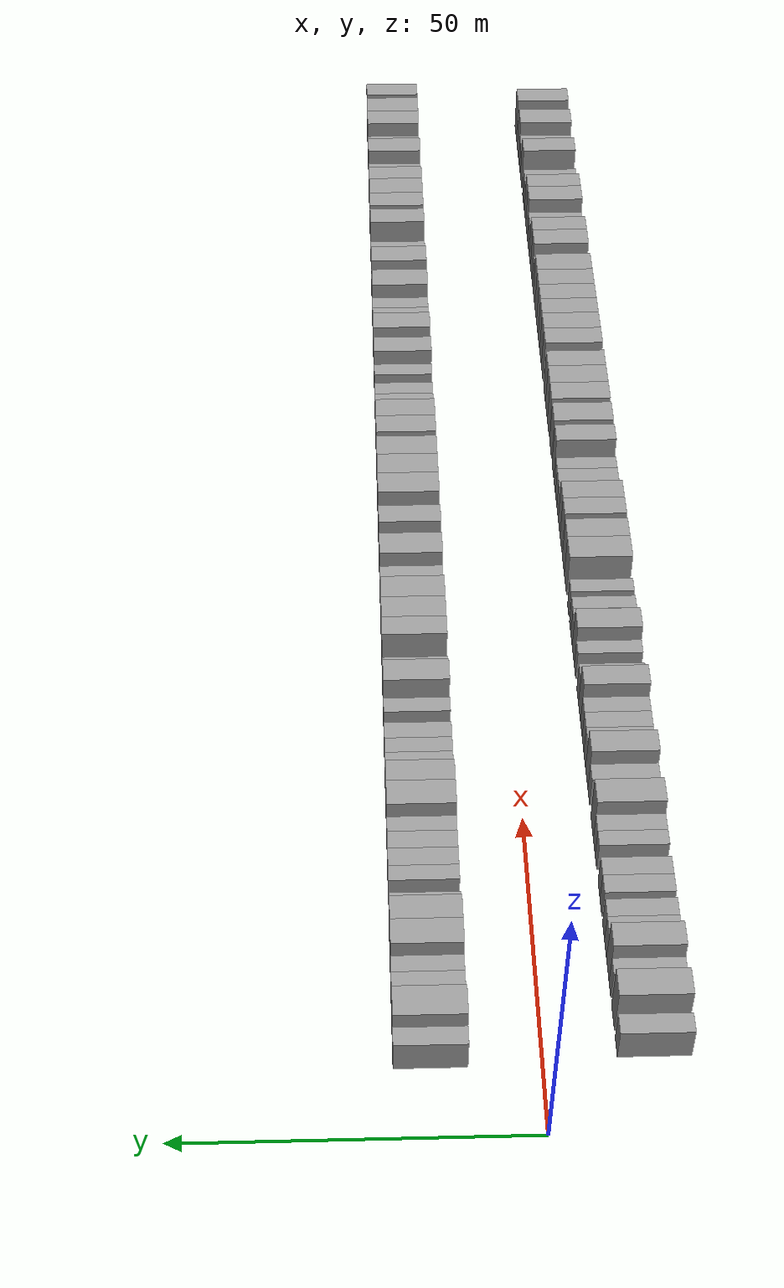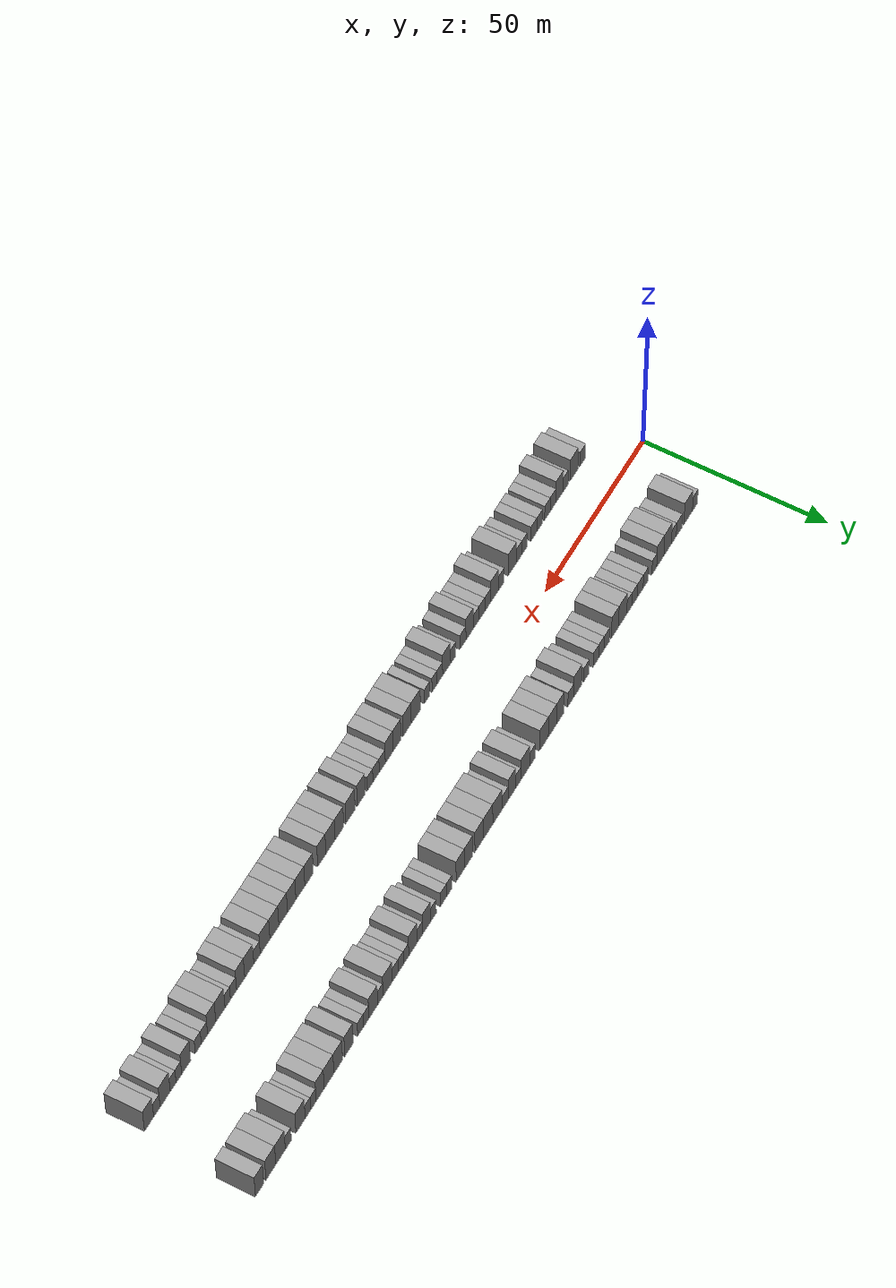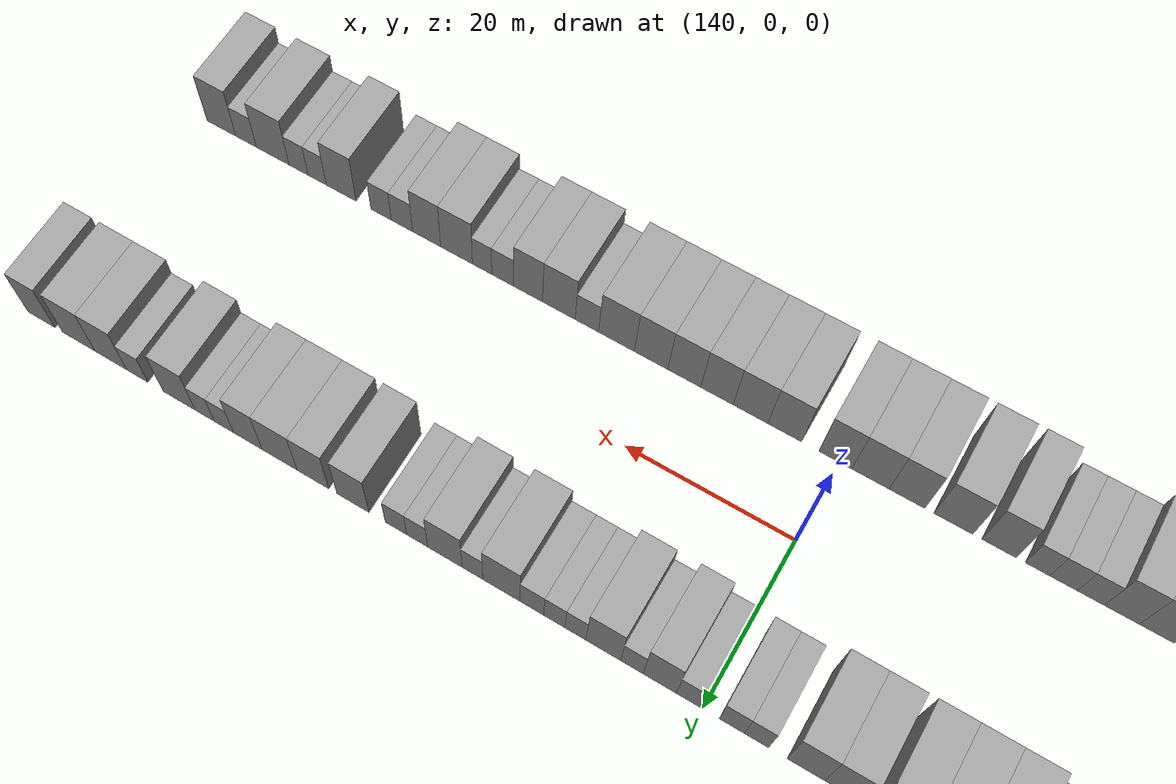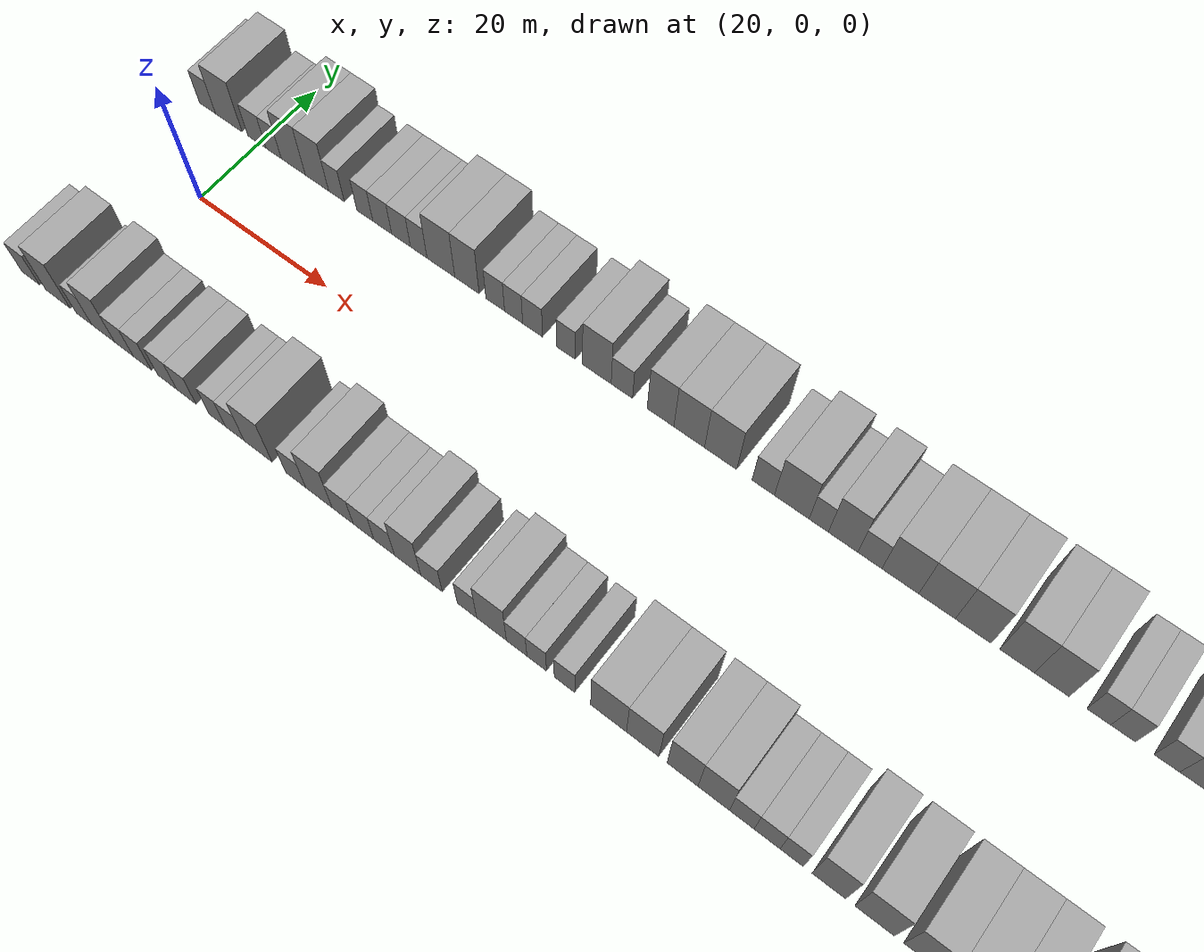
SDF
<sdf version="1.6">
 <world name="default">
  <scene>
   <sky><clouds><speed>12</speed></clouds></sky>
   <ambient>0.4 0.4 0.4 1</ambient>
   <background>0.7 0.7 0.7 1</background>
   <shadows>1</shadows>
  </scene>
  <gravity>0 0 -9.8066</gravity>
  <magnetic_field>6e-06 2.3e-05 -4.2e-05</magnetic_field>
  <physics default="0" name="default_physics" type="ode">
   <ode>
    <solver>
     <type>quick</type>
     <iters>10</iters>
     <sor>1.0</sor>
     <use_dynamic_moi_rescaling>0</use_dynamic_moi_rescaling>
    </solver>
    <constraints>
     <cfm>0</cfm>
     <erp>0.2</erp>
     <contact_max_correcting_vel>100</contact_max_correcting_vel>
     <contact_surface_layer>0.001</contact_surface_layer>
    </constraints>
   </ode>
   <max_step_size>0.004</max_step_size>
   <real_time_factor>1</real_time_factor>
   <real_time_update_rate>250</real_time_update_rate>
  </physics>
  <light name="sun" type="directional">
   <pose>0 0 10 0 0 0</pose>
   <diffuse>0.8 0.8 0.8 1</diffuse>
   <specular>0.2 0.2 0.2 1</specular>
   <attenuation>
    <range>1000</range>
    <constant>0.9</constant>
    <linear>0.01</linear>
    <quadratic>0.001</quadratic>
   </attenuation>
   <direction>-0.5 0.1 -0.9</direction>
  </light>
  <model name="building_1">
   <static>1</static>
   <pose>11.3570 15.0000 0 0.000000 0.000000 1.570796</pose>
   <link name="link">
    <pose>0 0 3.00 0 0 0</pose>
    <collision name="collision"><geometry><box><size>10.0000 2.7139 6.0000</size></box></geometry></collision>
    <visual name="visual">
     <cast_shadows>0</cast_shadows>
     <geometry><box><size>10.0000 2.7139 6.0000</size></box></geometry>
     <material>
      <script>
       <uri>model://grey_wall/materials/scripts</uri>
       <uri>model://grey_wall/materials/textures</uri>
       <name>vrc/grey_wall</name>
      </script>
     </material>
    </visual>
   </link>
  </model>
  <model name="building_2">
   <static>1</static>
   <pose>14.9309 15.0000 0 0.000000 0.000000 1.570796</pose>
   <link name="link">
    <pose>0 0 4.50 0 0 0</pose>
    <collision name="collision"><geometry><box><size>10.0000 4.4339 9.0000</size></box></geometry></collision>
    <visual name="visual">
     <cast_shadows>0</cast_shadows>
     <geometry><box><size>10.0000 4.4339 9.0000</size></box></geometry>
     <material>
      <script>
       <uri>model://grey_wall/materials/scripts</uri>
       <uri>model://grey_wall/materials/textures</uri>
       <name>vrc/grey_wall</name>
      </script>
     </material>
    </visual>
   </link>
  </model>
  <model name="building_3">
   <static>1</static>
   <pose>19.6361 15.0000 0 0.000000 0.000000 1.570796</pose>
   <link name="link">
    <pose>0 0 3.00 0 0 0</pose>
    <collision name="collision"><geometry><box><size>10.0000 2.9767 6.0000</size></box></geometry></collision>
    <visual name="visual">
     <cast_shadows>0</cast_shadows>
     <geometry><box><size>10.0000 2.9767 6.0000</size></box></geometry>
     <material>
      <script>
       <uri>model://grey_wall/materials/scripts</uri>
       <uri>model://grey_wall/materials/textures</uri>
       <name>vrc/grey_wall</name>
      </script>
     </material>
    </visual>
   </link>
  </model>
  <model name="building_4">
   <static>1</static>
   <pose>22.3674 15.0000 0 0.000000 0.000000 1.570796</pose>
   <link name="link">
    <pose>0 0 3.00 0 0 0</pose>
    <collision name="collision"><geometry><box><size>10.0000 2.4858 6.0000</size></box></geometry></collision>
    <visual name="visual">
     <cast_shadows>0</cast_shadows>
     <geometry><box><size>10.0000 2.4858 6.0000</size></box></geometry>
     <material>
      <script>
       <uri>model://grey_wall/materials/scripts</uri>
       <uri>model://grey_wall/materials/textures</uri>
       <name>vrc/grey_wall</name>
      </script>
     </material>
    </visual>
   </link>
  </model>
  <model name="building_5">
   <static>1</static>
   <pose>25.5686 15.0000 0 0.000000 0.000000 1.570796</pose>
   <link name="link">
    <pose>0 0 4.50 0 0 0</pose>
    <collision name="collision"><geometry><box><size>10.0000 3.9167 9.0000</size></box></geometry></collision>
    <visual name="visual">
     <cast_shadows>0</cast_shadows>
     <geometry><box><size>10.0000 3.9167 9.0000</size></box></geometry>
     <material>
      <script>
       <uri>model://grey_wall/materials/scripts</uri>
       <uri>model://grey_wall/materials/textures</uri>
       <name>vrc/grey_wall</name>
      </script>
     </material>
    </visual>
   </link>
  </model>
  <model name="building_6">
   <static>1</static>
   <pose>29.3910 15.0000 0 0.000000 0.000000 1.570796</pose>
   <link name="link">
    <pose>0 0 4.50 0 0 0</pose>
    <collision name="collision"><geometry><box><size>10.0000 3.7280 9.0000</size></box></geometry></collision>
    <visual name="visual">
     <cast_shadows>0</cast_shadows>
     <geometry><box><size>10.0000 3.7280 9.0000</size></box></geometry>
     <material>
      <script>
       <uri>model://grey_wall/materials/scripts</uri>
       <uri>model://grey_wall/materials/textures</uri>
       <name>vrc/grey_wall</name>
      </script>
     </material>
    </visual>
   </link>
  </model>
  <model name="building_7">
   <static>1</static>
   <pose>32.4861 15.0000 0 0.000000 0.000000 1.570796</pose>
   <link name="link">
    <pose>0 0 3.00 0 0 0</pose>
    <collision name="collision"><geometry><box><size>10.0000 2.4624 6.0000</size></box></geometry></collision>
    <visual name="visual">
     <cast_shadows>0</cast_shadows>
     <geometry><box><size>10.0000 2.4624 6.0000</size></box></geometry>
     <material>
      <script>
       <uri>model://grey_wall/materials/scripts</uri>
       <uri>model://grey_wall/materials/textures</uri>
       <name>vrc/grey_wall</name>
      </script>
     </material>
    </visual>
   </link>
  </model>
  <model name="building_8">
   <static>1</static>
   <pose>36.9637 15.0000 0 0.000000 0.000000 1.570796</pose>
   <link name="link">
    <pose>0 0 3.00 0 0 0</pose>
    <collision name="collision"><geometry><box><size>10.0000 2.4927 6.0000</size></box></geometry></collision>
    <visual name="visual">
     <cast_shadows>0</cast_shadows>
     <geometry><box><size>10.0000 2.4927 6.0000</size></box></geometry>
     <material>
      <script>
       <uri>model://grey_wall/materials/scripts</uri>
       <uri>model://grey_wall/materials/textures</uri>
       <name>vrc/grey_wall</name>
      </script>
     </material>
    </visual>
   </link>
  </model>
  <model name="building_9">
   <static>1</static>
   <pose>39.6702 15.0000 0 0.000000 0.000000 1.570796</pose>
   <link name="link">
    <pose>0 0 3.00 0 0 0</pose>
    <collision name="collision"><geometry><box><size>10.0000 2.9204 6.0000</size></box></geometry></collision>
    <visual name="visual">
     <cast_shadows>0</cast_shadows>
     <geometry><box><size>10.0000 2.9204 6.0000</size></box></geometry>
     <material>
      <script>
       <uri>model://grey_wall/materials/scripts</uri>
       <uri>model://grey_wall/materials/textures</uri>
       <name>vrc/grey_wall</name>
      </script>
     </material>
    </visual>
   </link>
  </model>
  <model name="building_10">
   <static>1</static>
   <pose>42.5760 15.0000 0 0.000000 0.000000 1.570796</pose>
   <link name="link">
    <pose>0 0 3.00 0 0 0</pose>
    <collision name="collision"><geometry><box><size>10.0000 2.8912 6.0000</size></box></geometry></collision>
    <visual name="visual">
     <cast_shadows>0</cast_shadows>
     <geometry><box><size>10.0000 2.8912 6.0000</size></box></geometry>
     <material>
      <script>
       <uri>model://grey_wall/materials/scripts</uri>
       <uri>model://grey_wall/materials/textures</uri>
       <name>vrc/grey_wall</name>
      </script>
     </material>
    </visual>
   </link>
  </model>
  <model name="building_11">
   <static>1</static>
   <pose>45.2801 15.0000 0 0.000000 0.000000 1.570796</pose>
   <link name="link">
    <pose>0 0 3.00 0 0 0</pose>
    <collision name="collision"><geometry><box><size>10.0000 2.5170 6.0000</size></box></geometry></collision>
    <visual name="visual">
     <cast_shadows>0</cast_shadows>
     <geometry><box><size>10.0000 2.5170 6.0000</size></box></geometry>
     <material>
      <script>
       <uri>model://grey_wall/materials/scripts</uri>
       <uri>model://grey_wall/materials/textures</uri>
       <name>vrc/grey_wall</name>
      </script>
     </material>
    </visual>
   </link>
  </model>
  <model name="building_12">
   <static>1</static>
   <pose>48.6344 15.0000 0 0.000000 0.000000 1.570796</pose>
   <link name="link">
    <pose>0 0 4.50 0 0 0</pose>
    <collision name="collision"><geometry><box><size>10.0000 4.1915 9.0000</size></box></geometry></collision>
    <visual name="visual">
     <cast_shadows>0</cast_shadows>
     <geometry><box><size>10.0000 4.1915 9.0000</size></box></geometry>
     <material>
      <script>
       <uri>model://grey_wall/materials/scripts</uri>
       <uri>model://grey_wall/materials/textures</uri>
       <name>vrc/grey_wall</name>
      </script>
     </material>
    </visual>
   </link>
  </model>
  <model name="building_13">
   <static>1</static>
   <pose>52.5369 15.0000 0 0.000000 0.000000 1.570796</pose>
   <link name="link">
    <pose>0 0 4.50 0 0 0</pose>
    <collision name="collision"><geometry><box><size>10.0000 3.6136 9.0000</size></box></geometry></collision>
    <visual name="visual">
     <cast_shadows>0</cast_shadows>
     <geometry><box><size>10.0000 3.6136 9.0000</size></box></geometry>
     <material>
      <script>
       <uri>model://grey_wall/materials/scripts</uri>
       <uri>model://grey_wall/materials/textures</uri>
       <name>vrc/grey_wall</name>
      </script>
     </material>
    </visual>
   </link>
  </model>
  <model name="building_14">
   <static>1</static>
   <pose>56.7094 15.0000 0 0.000000 0.000000 1.570796</pose>
   <link name="link">
    <pose>0 0 3.00 0 0 0</pose>
    <collision name="collision"><geometry><box><size>10.0000 2.7313 6.0000</size></box></geometry></collision>
    <visual name="visual">
     <cast_shadows>0</cast_shadows>
     <geometry><box><size>10.0000 2.7313 6.0000</size></box></geometry>
     <material>
      <script>
       <uri>model://grey_wall/materials/scripts</uri>
       <uri>model://grey_wall/materials/textures</uri>
       <name>vrc/grey_wall</name>
      </script>
     </material>
    </visual>
   </link>
  </model>
  <model name="building_15">
   <static>1</static>
   <pose>59.3927 15.0000 0 0.000000 0.000000 1.570796</pose>
   <link name="link">
    <pose>0 0 3.00 0 0 0</pose>
    <collision name="collision"><geometry><box><size>10.0000 2.6354 6.0000</size></box></geometry></collision>
    <visual name="visual">
     <cast_shadows>0</cast_shadows>
     <geometry><box><size>10.0000 2.6354 6.0000</size></box></geometry>
     <material>
      <script>
       <uri>model://grey_wall/materials/scripts</uri>
       <uri>model://grey_wall/materials/textures</uri>
       <name>vrc/grey_wall</name>
      </script>
     </material>
    </visual>
   </link>
  </model>
  <model name="building_16">
   <static>1</static>
   <pose>62.1425 15.0000 0 0.000000 0.000000 1.570796</pose>
   <link name="link">
    <pose>0 0 3.00 0 0 0</pose>
    <collision name="collision"><geometry><box><size>10.0000 2.8643 6.0000</size></box></geometry></collision>
    <visual name="visual">
     <cast_shadows>0</cast_shadows>
     <geometry><box><size>10.0000 2.8643 6.0000</size></box></geometry>
     <material>
      <script>
       <uri>model://grey_wall/materials/scripts</uri>
       <uri>model://grey_wall/materials/textures</uri>
       <name>vrc/grey_wall</name>
      </script>
     </material>
    </visual>
   </link>
  </model>
  <model name="building_17">
   <static>1</static>
   <pose>66.9048 15.0000 0 0.000000 0.000000 1.570796</pose>
   <link name="link">
    <pose>0 0 3.00 0 0 0</pose>
    <collision name="collision"><geometry><box><size>10.0000 2.6602 6.0000</size></box></geometry></collision>
    <visual name="visual">
     <cast_shadows>0</cast_shadows>
     <geometry><box><size>10.0000 2.6602 6.0000</size></box></geometry>
     <material>
      <script>
       <uri>model://grey_wall/materials/scripts</uri>
       <uri>model://grey_wall/materials/textures</uri>
       <name>vrc/grey_wall</name>
      </script>
     </material>
    </visual>
   </link>
  </model>
  <model name="building_18">
   <static>1</static>
   <pose>71.2412 15.0000 0 0.000000 0.000000 1.570796</pose>
   <link name="link">
    <pose>0 0 4.50 0 0 0</pose>
    <collision name="collision"><geometry><box><size>10.0000 4.0127 9.0000</size></box></geometry></collision>
    <visual name="visual">
     <cast_shadows>0</cast_shadows>
     <geometry><box><size>10.0000 4.0127 9.0000</size></box></geometry>
     <material>
      <script>
       <uri>model://grey_wall/materials/scripts</uri>
       <uri>model://grey_wall/materials/textures</uri>
       <name>vrc/grey_wall</name>
      </script>
     </material>
    </visual>
   </link>
  </model>
  <model name="building_19">
   <static>1</static>
   <pose>74.7267 15.0000 0 0.000000 0.000000 1.570796</pose>
   <link name="link">
    <pose>0 0 3.00 0 0 0</pose>
    <collision name="collision"><geometry><box><size>10.0000 2.9582 6.0000</size></box></geometry></collision>
    <visual name="visual">
     <cast_shadows>0</cast_shadows>
     <geometry><box><size>10.0000 2.9582 6.0000</size></box></geometry>
     <material>
      <script>
       <uri>model://grey_wall/materials/scripts</uri>
       <uri>model://grey_wall/materials/textures</uri>
       <name>vrc/grey_wall</name>
      </script>
     </material>
    </visual>
   </link>
  </model>
  <model name="building_20">
   <static>1</static>
   <pose>80.0178 15.0000 0 0.000000 0.000000 1.570796</pose>
   <link name="link">
    <pose>0 0 4.50 0 0 0</pose>
    <collision name="collision"><geometry><box><size>10.0000 3.6240 9.0000</size></box></geometry></collision>
    <visual name="visual">
     <cast_shadows>0</cast_shadows>
     <geometry><box><size>10.0000 3.6240 9.0000</size></box></geometry>
     <material>
      <script>
       <uri>model://grey_wall/materials/scripts</uri>
       <uri>model://grey_wall/materials/textures</uri>
       <name>vrc/grey_wall</name>
      </script>
     </material>
    </visual>
   </link>
  </model>
  <model name="building_21">
   <static>1</static>
   <pose>83.8820 15.0000 0 0.000000 0.000000 1.570796</pose>
   <link name="link">
    <pose>0 0 4.50 0 0 0</pose>
    <collision name="collision"><geometry><box><size>10.0000 4.1045 9.0000</size></box></geometry></collision>
    <visual name="visual">
     <cast_shadows>0</cast_shadows>
     <geometry><box><size>10.0000 4.1045 9.0000</size></box></geometry>
     <material>
      <script>
       <uri>model://grey_wall/materials/scripts</uri>
       <uri>model://grey_wall/materials/textures</uri>
       <name>vrc/grey_wall</name>
      </script>
     </material>
    </visual>
   </link>
  </model>
  <model name="building_22">
   <static>1</static>
   <pose>88.0626 15.0000 0 0.000000 0.000000 1.570796</pose>
   <link name="link">
    <pose>0 0 4.50 0 0 0</pose>
    <collision name="collision"><geometry><box><size>10.0000 4.2569 9.0000</size></box></geometry></collision>
    <visual name="visual">
     <cast_shadows>0</cast_shadows>
     <geometry><box><size>10.0000 4.2569 9.0000</size></box></geometry>
     <material>
      <script>
       <uri>model://grey_wall/materials/scripts</uri>
       <uri>model://grey_wall/materials/textures</uri>
       <name>vrc/grey_wall</name>
      </script>
     </material>
    </visual>
   </link>
  </model>
  <model name="building_23">
   <static>1</static>
   <pose>93.6376 15.0000 0 0.000000 0.000000 1.570796</pose>
   <link name="link">
    <pose>0 0 3.00 0 0 0</pose>
    <collision name="collision"><geometry><box><size>10.0000 2.8930 6.0000</size></box></geometry></collision>
    <visual name="visual">
     <cast_shadows>0</cast_shadows>
     <geometry><box><size>10.0000 2.8930 6.0000</size></box></geometry>
     <material>
      <script>
       <uri>model://grey_wall/materials/scripts</uri>
       <uri>model://grey_wall/materials/textures</uri>
       <name>vrc/grey_wall</name>
      </script>
     </material>
    </visual>
   </link>
  </model>
  <model name="building_24">
   <static>1</static>
   <pose>97.3048 15.0000 0 0.000000 0.000000 1.570796</pose>
   <link name="link">
    <pose>0 0 4.50 0 0 0</pose>
    <collision name="collision"><geometry><box><size>10.0000 4.4415 9.0000</size></box></geometry></collision>
    <visual name="visual">
     <cast_shadows>0</cast_shadows>
     <geometry><box><size>10.0000 4.4415 9.0000</size></box></geometry>
     <material>
      <script>
       <uri>model://grey_wall/materials/scripts</uri>
       <uri>model://grey_wall/materials/textures</uri>
       <name>vrc/grey_wall</name>
      </script>
     </material>
    </visual>
   </link>
  </model>
  <model name="building_25">
   <static>1</static>
   <pose>100.7398 15.0000 0 0.000000 0.000000 1.570796</pose>
   <link name="link">
    <pose>0 0 3.00 0 0 0</pose>
    <collision name="collision"><geometry><box><size>10.0000 2.4285 6.0000</size></box></geometry></collision>
    <visual name="visual">
     <cast_shadows>0</cast_shadows>
     <geometry><box><size>10.0000 2.4285 6.0000</size></box></geometry>
     <material>
      <script>
       <uri>model://grey_wall/materials/scripts</uri>
       <uri>model://grey_wall/materials/textures</uri>
       <name>vrc/grey_wall</name>
      </script>
     </material>
    </visual>
   </link>
  </model>
  <model name="building_26">
   <static>1</static>
   <pose>103.7903 15.0000 0 0.000000 0.000000 1.570796</pose>
   <link name="link">
    <pose>0 0 4.50 0 0 0</pose>
    <collision name="collision"><geometry><box><size>10.0000 3.6724 9.0000</size></box></geometry></collision>
    <visual name="visual">
     <cast_shadows>0</cast_shadows>
     <geometry><box><size>10.0000 3.6724 9.0000</size></box></geometry>
     <material>
      <script>
       <uri>model://grey_wall/materials/scripts</uri>
       <uri>model://grey_wall/materials/textures</uri>
       <name>vrc/grey_wall</name>
      </script>
     </material>
    </visual>
   </link>
  </model>
  <model name="building_27">
   <static>1</static>
   <pose>107.1217 15.0000 0 0.000000 0.000000 1.570796</pose>
   <link name="link">
    <pose>0 0 3.00 0 0 0</pose>
    <collision name="collision"><geometry><box><size>10.0000 2.9904 6.0000</size></box></geometry></collision>
    <visual name="visual">
     <cast_shadows>0</cast_shadows>
     <geometry><box><size>10.0000 2.9904 6.0000</size></box></geometry>
     <material>
      <script>
       <uri>model://grey_wall/materials/scripts</uri>
       <uri>model://grey_wall/materials/textures</uri>
       <name>vrc/grey_wall</name>
      </script>
     </material>
    </visual>
   </link>
  </model>
  <model name="building_28">
   <static>1</static>
   <pose>110.8591 15.0000 0 0.000000 0.000000 1.570796</pose>
   <link name="link">
    <pose>0 0 4.50 0 0 0</pose>
    <collision name="collision"><geometry><box><size>10.0000 4.4845 9.0000</size></box></geometry></collision>
    <visual name="visual">
     <cast_shadows>0</cast_shadows>
     <geometry><box><size>10.0000 4.4845 9.0000</size></box></geometry>
     <material>
      <script>
       <uri>model://grey_wall/materials/scripts</uri>
       <uri>model://grey_wall/materials/textures</uri>
       <name>vrc/grey_wall</name>
      </script>
     </material>
    </visual>
   </link>
  </model>
  <model name="building_29">
   <static>1</static>
   <pose>115.2992 15.0000 0 0.000000 0.000000 1.570796</pose>
   <link name="link">
    <pose>0 0 4.50 0 0 0</pose>
    <collision name="collision"><geometry><box><size>10.0000 4.3955 9.0000</size></box></geometry></collision>
    <visual name="visual">
     <cast_shadows>0</cast_shadows>
     <geometry><box><size>10.0000 4.3955 9.0000</size></box></geometry>
     <material>
      <script>
       <uri>model://grey_wall/materials/scripts</uri>
       <uri>model://grey_wall/materials/textures</uri>
       <name>vrc/grey_wall</name>
      </script>
     </material>
    </visual>
   </link>
  </model>
  <model name="building_30">
   <static>1</static>
   <pose>119.6165 15.0000 0 0.000000 0.000000 1.570796</pose>
   <link name="link">
    <pose>0 0 4.50 0 0 0</pose>
    <collision name="collision"><geometry><box><size>10.0000 4.2392 9.0000</size></box></geometry></collision>
    <visual name="visual">
     <cast_shadows>0</cast_shadows>
     <geometry><box><size>10.0000 4.2392 9.0000</size></box></geometry>
     <material>
      <script>
       <uri>model://grey_wall/materials/scripts</uri>
       <uri>model://grey_wall/materials/textures</uri>
       <name>vrc/grey_wall</name>
      </script>
     </material>
    </visual>
   </link>
  </model>
  <model name="building_31">
   <static>1</static>
   <pose>124.7347 15.0000 0 0.000000 0.000000 1.570796</pose>
   <link name="link">
    <pose>0 0 4.50 0 0 0</pose>
    <collision name="collision"><geometry><box><size>10.0000 3.9970 9.0000</size></box></geometry></collision>
    <visual name="visual">
     <cast_shadows>0</cast_shadows>
     <geometry><box><size>10.0000 3.9970 9.0000</size></box></geometry>
     <material>
      <script>
       <uri>model://grey_wall/materials/scripts</uri>
       <uri>model://grey_wall/materials/textures</uri>
       <name>vrc/grey_wall</name>
      </script>
     </material>
    </visual>
   </link>
  </model>
  <model name="building_32">
   <static>1</static>
   <pose>128.7281 15.0000 0 0.000000 0.000000 1.570796</pose>
   <link name="link">
    <pose>0 0 4.50 0 0 0</pose>
    <collision name="collision"><geometry><box><size>10.0000 3.9899 9.0000</size></box></geometry></collision>
    <visual name="visual">
     <cast_shadows>0</cast_shadows>
     <geometry><box><size>10.0000 3.9899 9.0000</size></box></geometry>
     <material>
      <script>
       <uri>model://grey_wall/materials/scripts</uri>
       <uri>model://grey_wall/materials/textures</uri>
       <name>vrc/grey_wall</name>
      </script>
     </material>
    </visual>
   </link>
  </model>
  <model name="building_33">
   <static>1</static>
   <pose>134.0501 15.0000 0 0.000000 0.000000 1.570796</pose>
   <link name="link">
    <pose>0 0 3.00 0 0 0</pose>
    <collision name="collision"><geometry><box><size>10.0000 2.6541 6.0000</size></box></geometry></collision>
    <visual name="visual">
     <cast_shadows>0</cast_shadows>
     <geometry><box><size>10.0000 2.6541 6.0000</size></box></geometry>
     <material>
      <script>
       <uri>model://grey_wall/materials/scripts</uri>
       <uri>model://grey_wall/materials/textures</uri>
       <name>vrc/grey_wall</name>
      </script>
     </material>
    </visual>
   </link>
  </model>
  <model name="building_34">
   <static>1</static>
   <pose>136.7619 15.0000 0 0.000000 0.000000 1.570796</pose>
   <link name="link">
    <pose>0 0 3.00 0 0 0</pose>
    <collision name="collision"><geometry><box><size>10.0000 2.7695 6.0000</size></box></geometry></collision>
    <visual name="visual">
     <cast_shadows>0</cast_shadows>
     <geometry><box><size>10.0000 2.7695 6.0000</size></box></geometry>
     <material>
      <script>
       <uri>model://grey_wall/materials/scripts</uri>
       <uri>model://grey_wall/materials/textures</uri>
       <name>vrc/grey_wall</name>
      </script>
     </material>
    </visual>
   </link>
  </model>
  <model name="building_35">
   <static>1</static>
   <pose>141.5453 15.0000 0 0.000000 0.000000 1.570796</pose>
   <link name="link">
    <pose>0 0 3.00 0 0 0</pose>
    <collision name="collision"><geometry><box><size>10.0000 2.7974 6.0000</size></box></geometry></collision>
    <visual name="visual">
     <cast_shadows>0</cast_shadows>
     <geometry><box><size>10.0000 2.7974 6.0000</size></box></geometry>
     <material>
      <script>
       <uri>model://grey_wall/materials/scripts</uri>
       <uri>model://grey_wall/materials/textures</uri>
       <name>vrc/grey_wall</name>
      </script>
     </material>
    </visual>
   </link>
  </model>
  <model name="building_36">
   <static>1</static>
   <pose>144.7961 15.0000 0 0.000000 0.000000 1.570796</pose>
   <link name="link">
    <pose>0 0 4.50 0 0 0</pose>
    <collision name="collision"><geometry><box><size>10.0000 3.7042 9.0000</size></box></geometry></collision>
    <visual name="visual">
     <cast_shadows>0</cast_shadows>
     <geometry><box><size>10.0000 3.7042 9.0000</size></box></geometry>
     <material>
      <script>
       <uri>model://grey_wall/materials/scripts</uri>
       <uri>model://grey_wall/materials/textures</uri>
       <name>vrc/grey_wall</name>
      </script>
     </material>
    </visual>
   </link>
  </model>
  <model name="building_37">
   <static>1</static>
   <pose>147.9257 15.0000 0 0.000000 0.000000 1.570796</pose>
   <link name="link">
    <pose>0 0 3.00 0 0 0</pose>
    <collision name="collision"><geometry><box><size>10.0000 2.5549 6.0000</size></box></geometry></collision>
    <visual name="visual">
     <cast_shadows>0</cast_shadows>
     <geometry><box><size>10.0000 2.5549 6.0000</size></box></geometry>
     <material>
      <script>
       <uri>model://grey_wall/materials/scripts</uri>
       <uri>model://grey_wall/materials/textures</uri>
       <name>vrc/grey_wall</name>
      </script>
     </material>
    </visual>
   </link>
  </model>
  <model name="building_38">
   <static>1</static>
   <pose>151.1870 15.0000 0 0.000000 0.000000 1.570796</pose>
   <link name="link">
    <pose>0 0 4.50 0 0 0</pose>
    <collision name="collision"><geometry><box><size>10.0000 3.9676 9.0000</size></box></geometry></collision>
    <visual name="visual">
     <cast_shadows>0</cast_shadows>
     <geometry><box><size>10.0000 3.9676 9.0000</size></box></geometry>
     <material>
      <script>
       <uri>model://grey_wall/materials/scripts</uri>
       <uri>model://grey_wall/materials/textures</uri>
       <name>vrc/grey_wall</name>
      </script>
     </material>
    </visual>
   </link>
  </model>
  <model name="building_39">
   <static>1</static>
   <pose>154.3847 15.0000 0 0.000000 0.000000 1.570796</pose>
   <link name="link">
    <pose>0 0 3.00 0 0 0</pose>
    <collision name="collision"><geometry><box><size>10.0000 2.4278 6.0000</size></box></geometry></collision>
    <visual name="visual">
     <cast_shadows>0</cast_shadows>
     <geometry><box><size>10.0000 2.4278 6.0000</size></box></geometry>
     <material>
      <script>
       <uri>model://grey_wall/materials/scripts</uri>
       <uri>model://grey_wall/materials/textures</uri>
       <name>vrc/grey_wall</name>
      </script>
     </material>
    </visual>
   </link>
  </model>
  <model name="building_40">
   <static>1</static>
   <pose>156.8276 15.0000 0 0.000000 0.000000 1.570796</pose>
   <link name="link">
    <pose>0 0 3.00 0 0 0</pose>
    <collision name="collision"><geometry><box><size>10.0000 2.4580 6.0000</size></box></geometry></collision>
    <visual name="visual">
     <cast_shadows>0</cast_shadows>
     <geometry><box><size>10.0000 2.4580 6.0000</size></box></geometry>
     <material>
      <script>
       <uri>model://grey_wall/materials/scripts</uri>
       <uri>model://grey_wall/materials/textures</uri>
       <name>vrc/grey_wall</name>
      </script>
     </material>
    </visual>
   </link>
  </model>
  <model name="building_41">
   <static>1</static>
   <pose>159.4426 15.0000 0 0.000000 0.000000 1.570796</pose>
   <link name="link">
    <pose>0 0 3.00 0 0 0</pose>
    <collision name="collision"><geometry><box><size>10.0000 2.7721 6.0000</size></box></geometry></collision>
    <visual name="visual">
     <cast_shadows>0</cast_shadows>
     <geometry><box><size>10.0000 2.7721 6.0000</size></box></geometry>
     <material>
      <script>
       <uri>model://grey_wall/materials/scripts</uri>
       <uri>model://grey_wall/materials/textures</uri>
       <name>vrc/grey_wall</name>
      </script>
     </material>
    </visual>
   </link>
  </model>
  <model name="building_42">
   <static>1</static>
   <pose>163.0122 15.0000 0 0.000000 0.000000 1.570796</pose>
   <link name="link">
    <pose>0 0 4.50 0 0 0</pose>
    <collision name="collision"><geometry><box><size>10.0000 4.3670 9.0000</size></box></geometry></collision>
    <visual name="visual">
     <cast_shadows>0</cast_shadows>
     <geometry><box><size>10.0000 4.3670 9.0000</size></box></geometry>
     <material>
      <script>
       <uri>model://grey_wall/materials/scripts</uri>
       <uri>model://grey_wall/materials/textures</uri>
       <name>vrc/grey_wall</name>
      </script>
     </material>
    </visual>
   </link>
  </model>
  <model name="building_43">
   <static>1</static>
   <pose>166.4237 15.0000 0 0.000000 0.000000 1.570796</pose>
   <link name="link">
    <pose>0 0 3.00 0 0 0</pose>
    <collision name="collision"><geometry><box><size>10.0000 2.4562 6.0000</size></box></geometry></collision>
    <visual name="visual">
     <cast_shadows>0</cast_shadows>
     <geometry><box><size>10.0000 2.4562 6.0000</size></box></geometry>
     <material>
      <script>
       <uri>model://grey_wall/materials/scripts</uri>
       <uri>model://grey_wall/materials/textures</uri>
       <name>vrc/grey_wall</name>
      </script>
     </material>
    </visual>
   </link>
  </model>
  <model name="building_44">
   <static>1</static>
   <pose>169.7165 15.0000 0 0.000000 0.000000 1.570796</pose>
   <link name="link">
    <pose>0 0 4.50 0 0 0</pose>
    <collision name="collision"><geometry><box><size>10.0000 4.1293 9.0000</size></box></geometry></collision>
    <visual name="visual">
     <cast_shadows>0</cast_shadows>
     <geometry><box><size>10.0000 4.1293 9.0000</size></box></geometry>
     <material>
      <script>
       <uri>model://grey_wall/materials/scripts</uri>
       <uri>model://grey_wall/materials/textures</uri>
       <name>vrc/grey_wall</name>
      </script>
     </material>
    </visual>
   </link>
  </model>
  <model name="building_45">
   <static>1</static>
   <pose>173.0395 15.0000 0 0.000000 0.000000 1.570796</pose>
   <link name="link">
    <pose>0 0 3.00 0 0 0</pose>
    <collision name="collision"><geometry><box><size>10.0000 2.5167 6.0000</size></box></geometry></collision>
    <visual name="visual">
     <cast_shadows>0</cast_shadows>
     <geometry><box><size>10.0000 2.5167 6.0000</size></box></geometry>
     <material>
      <script>
       <uri>model://grey_wall/materials/scripts</uri>
       <uri>model://grey_wall/materials/textures</uri>
       <name>vrc/grey_wall</name>
      </script>
     </material>
    </visual>
   </link>
  </model>
  <model name="building_46">
   <static>1</static>
   <pose>175.6132 15.0000 0 0.000000 0.000000 1.570796</pose>
   <link name="link">
    <pose>0 0 3.00 0 0 0</pose>
    <collision name="collision"><geometry><box><size>10.0000 2.6307 6.0000</size></box></geometry></collision>
    <visual name="visual">
     <cast_shadows>0</cast_shadows>
     <geometry><box><size>10.0000 2.6307 6.0000</size></box></geometry>
     <material>
      <script>
       <uri>model://grey_wall/materials/scripts</uri>
       <uri>model://grey_wall/materials/textures</uri>
       <name>vrc/grey_wall</name>
      </script>
     </material>
    </visual>
   </link>
  </model>
  <model name="building_47">
   <static>1</static>
   <pose>180.9091 15.0000 0 0.000000 0.000000 1.570796</pose>
   <link name="link">
    <pose>0 0 4.50 0 0 0</pose>
    <collision name="collision"><geometry><box><size>10.0000 3.9610 9.0000</size></box></geometry></collision>
    <visual name="visual">
     <cast_shadows>0</cast_shadows>
     <geometry><box><size>10.0000 3.9610 9.0000</size></box></geometry>
     <material>
      <script>
       <uri>model://grey_wall/materials/scripts</uri>
       <uri>model://grey_wall/materials/textures</uri>
       <name>vrc/grey_wall</name>
      </script>
     </material>
    </visual>
   </link>
  </model>
  <model name="building_48">
   <static>1</static>
   <pose>185.8766 15.0000 0 0.000000 0.000000 1.570796</pose>
   <link name="link">
    <pose>0 0 4.50 0 0 0</pose>
    <collision name="collision"><geometry><box><size>10.0000 3.9740 9.0000</size></box></geometry></collision>
    <visual name="visual">
     <cast_shadows>0</cast_shadows>
     <geometry><box><size>10.0000 3.9740 9.0000</size></box></geometry>
     <material>
      <script>
       <uri>model://grey_wall/materials/scripts</uri>
       <uri>model://grey_wall/materials/textures</uri>
       <name>vrc/grey_wall</name>
      </script>
     </material>
    </visual>
   </link>
  </model>
  <model name="building_49">
   <static>1</static>
   <pose>190.0757 15.0000 0 0.000000 0.000000 1.570796</pose>
   <link name="link">
    <pose>0 0 4.50 0 0 0</pose>
    <collision name="collision"><geometry><box><size>10.0000 4.4241 9.0000</size></box></geometry></collision>
    <visual name="visual">
     <cast_shadows>0</cast_shadows>
     <geometry><box><size>10.0000 4.4241 9.0000</size></box></geometry>
     <material>
      <script>
       <uri>model://grey_wall/materials/scripts</uri>
       <uri>model://grey_wall/materials/textures</uri>
       <name>vrc/grey_wall</name>
      </script>
     </material>
    </visual>
   </link>
  </model>
  <model name="building_50">
   <static>1</static>
   <pose>194.1069 15.0000 0 0.000000 0.000000 1.570796</pose>
   <link name="link">
    <pose>0 0 4.50 0 0 0</pose>
    <collision name="collision"><geometry><box><size>10.0000 3.6383 9.0000</size></box></geometry></collision>
    <visual name="visual">
     <cast_shadows>0</cast_shadows>
     <geometry><box><size>10.0000 3.6383 9.0000</size></box></geometry>
     <material>
      <script>
       <uri>model://grey_wall/materials/scripts</uri>
       <uri>model://grey_wall/materials/textures</uri>
       <name>vrc/grey_wall</name>
      </script>
     </material>
    </visual>
   </link>
  </model>
  <model name="building_51">
   <static>1</static>
   <pose>197.1654 15.0000 0 0.000000 0.000000 1.570796</pose>
   <link name="link">
    <pose>0 0 3.00 0 0 0</pose>
    <collision name="collision"><geometry><box><size>10.0000 2.4788 6.0000</size></box></geometry></collision>
    <visual name="visual">
     <cast_shadows>0</cast_shadows>
     <geometry><box><size>10.0000 2.4788 6.0000</size></box></geometry>
     <material>
      <script>
       <uri>model://grey_wall/materials/scripts</uri>
       <uri>model://grey_wall/materials/textures</uri>
       <name>vrc/grey_wall</name>
      </script>
     </material>
    </visual>
   </link>
  </model>
  <model name="building_52">
   <static>1</static>
   <pose>199.6519 15.0000 0 0.000000 0.000000 1.570796</pose>
   <link name="link">
    <pose>0 0 3.00 0 0 0</pose>
    <collision name="collision"><geometry><box><size>10.0000 2.4940 6.0000</size></box></geometry></collision>
    <visual name="visual">
     <cast_shadows>0</cast_shadows>
     <geometry><box><size>10.0000 2.4940 6.0000</size></box></geometry>
     <material>
      <script>
       <uri>model://grey_wall/materials/scripts</uri>
       <uri>model://grey_wall/materials/textures</uri>
       <name>vrc/grey_wall</name>
      </script>
     </material>
    </visual>
   </link>
  </model>
  <model name="building_53">
   <static>1</static>
   <pose>202.9938 15.0000 0 0.000000 0.000000 1.570796</pose>
   <link name="link">
    <pose>0 0 4.50 0 0 0</pose>
    <collision name="collision"><geometry><box><size>10.0000 4.1898 9.0000</size></box></geometry></collision>
    <visual name="visual">
     <cast_shadows>0</cast_shadows>
     <geometry><box><size>10.0000 4.1898 9.0000</size></box></geometry>
     <material>
      <script>
       <uri>model://grey_wall/materials/scripts</uri>
       <uri>model://grey_wall/materials/textures</uri>
       <name>vrc/grey_wall</name>
      </script>
     </material>
    </visual>
   </link>
  </model>
  <model name="building_54">
   <static>1</static>
   <pose>208.4833 15.0000 0 0.000000 0.000000 1.570796</pose>
   <link name="link">
    <pose>0 0 3.00 0 0 0</pose>
    <collision name="collision"><geometry><box><size>10.0000 2.7892 6.0000</size></box></geometry></collision>
    <visual name="visual">
     <cast_shadows>0</cast_shadows>
     <geometry><box><size>10.0000 2.7892 6.0000</size></box></geometry>
     <material>
      <script>
       <uri>model://grey_wall/materials/scripts</uri>
       <uri>model://grey_wall/materials/textures</uri>
       <name>vrc/grey_wall</name>
      </script>
     </material>
    </visual>
   </link>
  </model>
  <model name="building_55">
   <static>1</static>
   <pose>212.0010 15.0000 0 0.000000 0.000000 1.570796</pose>
   <link name="link">
    <pose>0 0 4.50 0 0 0</pose>
    <collision name="collision"><geometry><box><size>10.0000 4.2462 9.0000</size></box></geometry></collision>
    <visual name="visual">
     <cast_shadows>0</cast_shadows>
     <geometry><box><size>10.0000 4.2462 9.0000</size></box></geometry>
     <material>
      <script>
       <uri>model://grey_wall/materials/scripts</uri>
       <uri>model://grey_wall/materials/textures</uri>
       <name>vrc/grey_wall</name>
      </script>
     </material>
    </visual>
   </link>
  </model>
  <model name="building_56">
   <static>1</static>
   <pose>216.3289 15.0000 0 0.000000 0.000000 1.570796</pose>
   <link name="link">
    <pose>0 0 4.50 0 0 0</pose>
    <collision name="collision"><geometry><box><size>10.0000 4.4097 9.0000</size></box></geometry></collision>
    <visual name="visual">
     <cast_shadows>0</cast_shadows>
     <geometry><box><size>10.0000 4.4097 9.0000</size></box></geometry>
     <material>
      <script>
       <uri>model://grey_wall/materials/scripts</uri>
       <uri>model://grey_wall/materials/textures</uri>
       <name>vrc/grey_wall</name>
      </script>
     </material>
    </visual>
   </link>
  </model>
  <model name="building_57">
   <static>1</static>
   <pose>221.3847 15.0000 0 0.000000 0.000000 1.570796</pose>
   <link name="link">
    <pose>0 0 4.50 0 0 0</pose>
    <collision name="collision"><geometry><box><size>10.0000 3.7019 9.0000</size></box></geometry></collision>
    <visual name="visual">
     <cast_shadows>0</cast_shadows>
     <geometry><box><size>10.0000 3.7019 9.0000</size></box></geometry>
     <material>
      <script>
       <uri>model://grey_wall/materials/scripts</uri>
       <uri>model://grey_wall/materials/textures</uri>
       <name>vrc/grey_wall</name>
      </script>
     </material>
    </visual>
   </link>
  </model>
  <model name="building_58">
   <static>1</static>
   <pose>12.4755 -15.0000 0 0.000000 0.000000 1.570796</pose>
   <link name="link">
    <pose>0 0 3.00 0 0 0</pose>
    <collision name="collision"><geometry><box><size>10.0000 2.9509 6.0000</size></box></geometry></collision>
    <visual name="visual">
     <cast_shadows>0</cast_shadows>
     <geometry><box><size>10.0000 2.9509 6.0000</size></box></geometry>
     <material>
      <script>
       <uri>model://grey_wall/materials/scripts</uri>
       <uri>model://grey_wall/materials/textures</uri>
       <name>vrc/grey_wall</name>
      </script>
     </material>
    </visual>
   </link>
  </model>
  <model name="building_59">
   <static>1</static>
   <pose>16.9591 -15.0000 0 0.000000 0.000000 1.570796</pose>
   <link name="link">
    <pose>0 0 4.50 0 0 0</pose>
    <collision name="collision"><geometry><box><size>10.0000 4.0164 9.0000</size></box></geometry></collision>
    <visual name="visual">
     <cast_shadows>0</cast_shadows>
     <geometry><box><size>10.0000 4.0164 9.0000</size></box></geometry>
     <material>
      <script>
       <uri>model://grey_wall/materials/scripts</uri>
       <uri>model://grey_wall/materials/textures</uri>
       <name>vrc/grey_wall</name>
      </script>
     </material>
    </visual>
   </link>
  </model>
  <model name="building_60">
   <static>1</static>
   <pose>21.2301 -15.0000 0 0.000000 0.000000 1.570796</pose>
   <link name="link">
    <pose>0 0 3.00 0 0 0</pose>
    <collision name="collision"><geometry><box><size>10.0000 2.5254 6.0000</size></box></geometry></collision>
    <visual name="visual">
     <cast_shadows>0</cast_shadows>
     <geometry><box><size>10.0000 2.5254 6.0000</size></box></geometry>
     <material>
      <script>
       <uri>model://grey_wall/materials/scripts</uri>
       <uri>model://grey_wall/materials/textures</uri>
       <name>vrc/grey_wall</name>
      </script>
     </material>
    </visual>
   </link>
  </model>
  <model name="building_61">
   <static>1</static>
   <pose>24.3298 -15.0000 0 0.000000 0.000000 1.570796</pose>
   <link name="link">
    <pose>0 0 4.50 0 0 0</pose>
    <collision name="collision"><geometry><box><size>10.0000 3.6741 9.0000</size></box></geometry></collision>
    <visual name="visual">
     <cast_shadows>0</cast_shadows>
     <geometry><box><size>10.0000 3.6741 9.0000</size></box></geometry>
     <material>
      <script>
       <uri>model://grey_wall/materials/scripts</uri>
       <uri>model://grey_wall/materials/textures</uri>
       <name>vrc/grey_wall</name>
      </script>
     </material>
    </visual>
   </link>
  </model>
  <model name="building_62">
   <static>1</static>
   <pose>27.6396 -15.0000 0 0.000000 0.000000 1.570796</pose>
   <link name="link">
    <pose>0 0 3.00 0 0 0</pose>
    <collision name="collision"><geometry><box><size>10.0000 2.9454 6.0000</size></box></geometry></collision>
    <visual name="visual">
     <cast_shadows>0</cast_shadows>
     <geometry><box><size>10.0000 2.9454 6.0000</size></box></geometry>
     <material>
      <script>
       <uri>model://grey_wall/materials/scripts</uri>
       <uri>model://grey_wall/materials/textures</uri>
       <name>vrc/grey_wall</name>
      </script>
     </material>
    </visual>
   </link>
  </model>
  <model name="building_63">
   <static>1</static>
   <pose>30.5293 -15.0000 0 0.000000 0.000000 1.570796</pose>
   <link name="link">
    <pose>0 0 3.00 0 0 0</pose>
    <collision name="collision"><geometry><box><size>10.0000 2.8340 6.0000</size></box></geometry></collision>
    <visual name="visual">
     <cast_shadows>0</cast_shadows>
     <geometry><box><size>10.0000 2.8340 6.0000</size></box></geometry>
     <material>
      <script>
       <uri>model://grey_wall/materials/scripts</uri>
       <uri>model://grey_wall/materials/textures</uri>
       <name>vrc/grey_wall</name>
      </script>
     </material>
    </visual>
   </link>
  </model>
  <model name="building_64">
   <static>1</static>
   <pose>34.4199 -15.0000 0 0.000000 0.000000 1.570796</pose>
   <link name="link">
    <pose>0 0 3.00 0 0 0</pose>
    <collision name="collision"><geometry><box><size>10.0000 2.9471 6.0000</size></box></geometry></collision>
    <visual name="visual">
     <cast_shadows>0</cast_shadows>
     <geometry><box><size>10.0000 2.9471 6.0000</size></box></geometry>
     <material>
      <script>
       <uri>model://grey_wall/materials/scripts</uri>
       <uri>model://grey_wall/materials/textures</uri>
       <name>vrc/grey_wall</name>
      </script>
     </material>
    </visual>
   </link>
  </model>
  <model name="building_65">
   <static>1</static>
   <pose>37.3664 -15.0000 0 0.000000 0.000000 1.570796</pose>
   <link name="link">
    <pose>0 0 3.00 0 0 0</pose>
    <collision name="collision"><geometry><box><size>10.0000 2.9459 6.0000</size></box></geometry></collision>
    <visual name="visual">
     <cast_shadows>0</cast_shadows>
     <geometry><box><size>10.0000 2.9459 6.0000</size></box></geometry>
     <material>
      <script>
       <uri>model://grey_wall/materials/scripts</uri>
       <uri>model://grey_wall/materials/textures</uri>
       <name>vrc/grey_wall</name>
      </script>
     </material>
    </visual>
   </link>
  </model>
  <model name="building_66">
   <static>1</static>
   <pose>42.0979 -15.0000 0 0.000000 0.000000 1.570796</pose>
   <link name="link">
    <pose>0 0 3.00 0 0 0</pose>
    <collision name="collision"><geometry><box><size>10.0000 2.5170 6.0000</size></box></geometry></collision>
    <visual name="visual">
     <cast_shadows>0</cast_shadows>
     <geometry><box><size>10.0000 2.5170 6.0000</size></box></geometry>
     <material>
      <script>
       <uri>model://grey_wall/materials/scripts</uri>
       <uri>model://grey_wall/materials/textures</uri>
       <name>vrc/grey_wall</name>
      </script>
     </material>
    </visual>
   </link>
  </model>
  <model name="building_67">
   <static>1</static>
   <pose>44.7437 -15.0000 0 0.000000 0.000000 1.570796</pose>
   <link name="link">
    <pose>0 0 3.00 0 0 0</pose>
    <collision name="collision"><geometry><box><size>10.0000 2.7746 6.0000</size></box></geometry></collision>
    <visual name="visual">
     <cast_shadows>0</cast_shadows>
     <geometry><box><size>10.0000 2.7746 6.0000</size></box></geometry>
     <material>
      <script>
       <uri>model://grey_wall/materials/scripts</uri>
       <uri>model://grey_wall/materials/textures</uri>
       <name>vrc/grey_wall</name>
      </script>
     </material>
    </visual>
   </link>
  </model>
  <model name="building_68">
   <static>1</static>
   <pose>48.1759 -15.0000 0 0.000000 0.000000 1.570796</pose>
   <link name="link">
    <pose>0 0 4.50 0 0 0</pose>
    <collision name="collision"><geometry><box><size>10.0000 4.0898 9.0000</size></box></geometry></collision>
    <visual name="visual">
     <cast_shadows>0</cast_shadows>
     <geometry><box><size>10.0000 4.0898 9.0000</size></box></geometry>
     <material>
      <script>
       <uri>model://grey_wall/materials/scripts</uri>
       <uri>model://grey_wall/materials/textures</uri>
       <name>vrc/grey_wall</name>
      </script>
     </material>
    </visual>
   </link>
  </model>
  <model name="building_69">
   <static>1</static>
   <pose>53.6829 -15.0000 0 0.000000 0.000000 1.570796</pose>
   <link name="link">
    <pose>0 0 3.00 0 0 0</pose>
    <collision name="collision"><geometry><box><size>10.0000 2.9241 6.0000</size></box></geometry></collision>
    <visual name="visual">
     <cast_shadows>0</cast_shadows>
     <geometry><box><size>10.0000 2.9241 6.0000</size></box></geometry>
     <material>
      <script>
       <uri>model://grey_wall/materials/scripts</uri>
       <uri>model://grey_wall/materials/textures</uri>
       <name>vrc/grey_wall</name>
      </script>
     </material>
    </visual>
   </link>
  </model>
  <model name="building_70">
   <static>1</static>
   <pose>57.0336 -15.0000 0 0.000000 0.000000 1.570796</pose>
   <link name="link">
    <pose>0 0 4.50 0 0 0</pose>
    <collision name="collision"><geometry><box><size>10.0000 3.7774 9.0000</size></box></geometry></collision>
    <visual name="visual">
     <cast_shadows>0</cast_shadows>
     <geometry><box><size>10.0000 3.7774 9.0000</size></box></geometry>
     <material>
      <script>
       <uri>model://grey_wall/materials/scripts</uri>
       <uri>model://grey_wall/materials/textures</uri>
       <name>vrc/grey_wall</name>
      </script>
     </material>
    </visual>
   </link>
  </model>
  <model name="building_71">
   <static>1</static>
   <pose>60.4218 -15.0000 0 0.000000 0.000000 1.570796</pose>
   <link name="link">
    <pose>0 0 3.00 0 0 0</pose>
    <collision name="collision"><geometry><box><size>10.0000 2.9990 6.0000</size></box></geometry></collision>
    <visual name="visual">
     <cast_shadows>0</cast_shadows>
     <geometry><box><size>10.0000 2.9990 6.0000</size></box></geometry>
     <material>
      <script>
       <uri>model://grey_wall/materials/scripts</uri>
       <uri>model://grey_wall/materials/textures</uri>
       <name>vrc/grey_wall</name>
      </script>
     </material>
    </visual>
   </link>
  </model>
  <model name="building_72">
   <static>1</static>
   <pose>63.3778 -15.0000 0 0.000000 0.000000 1.570796</pose>
   <link name="link">
    <pose>0 0 3.00 0 0 0</pose>
    <collision name="collision"><geometry><box><size>10.0000 2.9130 6.0000</size></box></geometry></collision>
    <visual name="visual">
     <cast_shadows>0</cast_shadows>
     <geometry><box><size>10.0000 2.9130 6.0000</size></box></geometry>
     <material>
      <script>
       <uri>model://grey_wall/materials/scripts</uri>
       <uri>model://grey_wall/materials/textures</uri>
       <name>vrc/grey_wall</name>
      </script>
     </material>
    </visual>
   </link>
  </model>
  <model name="building_73">
   <static>1</static>
   <pose>66.2464 -15.0000 0 0.000000 0.000000 1.570796</pose>
   <link name="link">
    <pose>0 0 3.00 0 0 0</pose>
    <collision name="collision"><geometry><box><size>10.0000 2.8241 6.0000</size></box></geometry></collision>
    <visual name="visual">
     <cast_shadows>0</cast_shadows>
     <geometry><box><size>10.0000 2.8241 6.0000</size></box></geometry>
     <material>
      <script>
       <uri>model://grey_wall/materials/scripts</uri>
       <uri>model://grey_wall/materials/textures</uri>
       <name>vrc/grey_wall</name>
      </script>
     </material>
    </visual>
   </link>
  </model>
  <model name="building_74">
   <static>1</static>
   <pose>69.4696 -15.0000 0 0.000000 0.000000 1.570796</pose>
   <link name="link">
    <pose>0 0 4.50 0 0 0</pose>
    <collision name="collision"><geometry><box><size>10.0000 3.6223 9.0000</size></box></geometry></collision>
    <visual name="visual">
     <cast_shadows>0</cast_shadows>
     <geometry><box><size>10.0000 3.6223 9.0000</size></box></geometry>
     <material>
      <script>
       <uri>model://grey_wall/materials/scripts</uri>
       <uri>model://grey_wall/materials/textures</uri>
       <name>vrc/grey_wall</name>
      </script>
     </material>
    </visual>
   </link>
  </model>
  <model name="building_75">
   <static>1</static>
   <pose>72.7425 -15.0000 0 0.000000 0.000000 1.570796</pose>
   <link name="link">
    <pose>0 0 3.00 0 0 0</pose>
    <collision name="collision"><geometry><box><size>10.0000 2.9235 6.0000</size></box></geometry></collision>
    <visual name="visual">
     <cast_shadows>0</cast_shadows>
     <geometry><box><size>10.0000 2.9235 6.0000</size></box></geometry>
     <material>
      <script>
       <uri>model://grey_wall/materials/scripts</uri>
       <uri>model://grey_wall/materials/textures</uri>
       <name>vrc/grey_wall</name>
      </script>
     </material>
    </visual>
   </link>
  </model>
  <model name="building_76">
   <static>1</static>
   <pose>77.4930 -15.0000 0 0.000000 0.000000 1.570796</pose>
   <link name="link">
    <pose>0 0 3.00 0 0 0</pose>
    <collision name="collision"><geometry><box><size>10.0000 2.5774 6.0000</size></box></geometry></collision>
    <visual name="visual">
     <cast_shadows>0</cast_shadows>
     <geometry><box><size>10.0000 2.5774 6.0000</size></box></geometry>
     <material>
      <script>
       <uri>model://grey_wall/materials/scripts</uri>
       <uri>model://grey_wall/materials/textures</uri>
       <name>vrc/grey_wall</name>
      </script>
     </material>
    </visual>
   </link>
  </model>
  <model name="building_77">
   <static>1</static>
   <pose>80.7395 -15.0000 0 0.000000 0.000000 1.570796</pose>
   <link name="link">
    <pose>0 0 4.50 0 0 0</pose>
    <collision name="collision"><geometry><box><size>10.0000 3.9156 9.0000</size></box></geometry></collision>
    <visual name="visual">
     <cast_shadows>0</cast_shadows>
     <geometry><box><size>10.0000 3.9156 9.0000</size></box></geometry>
     <material>
      <script>
       <uri>model://grey_wall/materials/scripts</uri>
       <uri>model://grey_wall/materials/textures</uri>
       <name>vrc/grey_wall</name>
      </script>
     </material>
    </visual>
   </link>
  </model>
  <model name="building_78">
   <static>1</static>
   <pose>84.0360 -15.0000 0 0.000000 0.000000 1.570796</pose>
   <link name="link">
    <pose>0 0 3.00 0 0 0</pose>
    <collision name="collision"><geometry><box><size>10.0000 2.6775 6.0000</size></box></geometry></collision>
    <visual name="visual">
     <cast_shadows>0</cast_shadows>
     <geometry><box><size>10.0000 2.6775 6.0000</size></box></geometry>
     <material>
      <script>
       <uri>model://grey_wall/materials/scripts</uri>
       <uri>model://grey_wall/materials/textures</uri>
       <name>vrc/grey_wall</name>
      </script>
     </material>
    </visual>
   </link>
  </model>
  <model name="building_79">
   <static>1</static>
   <pose>86.6370 -15.0000 0 0.000000 0.000000 1.570796</pose>
   <link name="link">
    <pose>0 0 3.00 0 0 0</pose>
    <collision name="collision"><geometry><box><size>10.0000 2.5244 6.0000</size></box></geometry></collision>
    <visual name="visual">
     <cast_shadows>0</cast_shadows>
     <geometry><box><size>10.0000 2.5244 6.0000</size></box></geometry>
     <material>
      <script>
       <uri>model://grey_wall/materials/scripts</uri>
       <uri>model://grey_wall/materials/textures</uri>
       <name>vrc/grey_wall</name>
      </script>
     </material>
    </visual>
   </link>
  </model>
  <model name="building_80">
   <static>1</static>
   <pose>90.1990 -15.0000 0 0.000000 0.000000 1.570796</pose>
   <link name="link">
    <pose>0 0 3.00 0 0 0</pose>
    <collision name="collision"><geometry><box><size>10.0000 2.5996 6.0000</size></box></geometry></collision>
    <visual name="visual">
     <cast_shadows>0</cast_shadows>
     <geometry><box><size>10.0000 2.5996 6.0000</size></box></geometry>
     <material>
      <script>
       <uri>model://grey_wall/materials/scripts</uri>
       <uri>model://grey_wall/materials/textures</uri>
       <name>vrc/grey_wall</name>
      </script>
     </material>
    </visual>
   </link>
  </model>
  <model name="building_81">
   <static>1</static>
   <pose>95.7273 -15.0000 0 0.000000 0.000000 1.570796</pose>
   <link name="link">
    <pose>0 0 4.50 0 0 0</pose>
    <collision name="collision"><geometry><box><size>10.0000 4.4570 9.0000</size></box></geometry></collision>
    <visual name="visual">
     <cast_shadows>0</cast_shadows>
     <geometry><box><size>10.0000 4.4570 9.0000</size></box></geometry>
     <material>
      <script>
       <uri>model://grey_wall/materials/scripts</uri>
       <uri>model://grey_wall/materials/textures</uri>
       <name>vrc/grey_wall</name>
      </script>
     </material>
    </visual>
   </link>
  </model>
  <model name="building_82">
   <static>1</static>
   <pose>99.9507 -15.0000 0 0.000000 0.000000 1.570796</pose>
   <link name="link">
    <pose>0 0 4.50 0 0 0</pose>
    <collision name="collision"><geometry><box><size>10.0000 3.9898 9.0000</size></box></geometry></collision>
    <visual name="visual">
     <cast_shadows>0</cast_shadows>
     <geometry><box><size>10.0000 3.9898 9.0000</size></box></geometry>
     <material>
      <script>
       <uri>model://grey_wall/materials/scripts</uri>
       <uri>model://grey_wall/materials/textures</uri>
       <name>vrc/grey_wall</name>
      </script>
     </material>
    </visual>
   </link>
  </model>
  <model name="building_83">
   <static>1</static>
   <pose>104.8039 -15.0000 0 0.000000 0.000000 1.570796</pose>
   <link name="link">
    <pose>0 0 4.50 0 0 0</pose>
    <collision name="collision"><geometry><box><size>10.0000 3.7165 9.0000</size></box></geometry></collision>
    <visual name="visual">
     <cast_shadows>0</cast_shadows>
     <geometry><box><size>10.0000 3.7165 9.0000</size></box></geometry>
     <material>
      <script>
       <uri>model://grey_wall/materials/scripts</uri>
       <uri>model://grey_wall/materials/textures</uri>
       <name>vrc/grey_wall</name>
      </script>
     </material>
    </visual>
   </link>
  </model>
  <model name="building_84">
   <static>1</static>
   <pose>108.5324 -15.0000 0 0.000000 0.000000 1.570796</pose>
   <link name="link">
    <pose>0 0 4.50 0 0 0</pose>
    <collision name="collision"><geometry><box><size>10.0000 3.7405 9.0000</size></box></geometry></collision>
    <visual name="visual">
     <cast_shadows>0</cast_shadows>
     <geometry><box><size>10.0000 3.7405 9.0000</size></box></geometry>
     <material>
      <script>
       <uri>model://grey_wall/materials/scripts</uri>
       <uri>model://grey_wall/materials/textures</uri>
       <name>vrc/grey_wall</name>
      </script>
     </material>
    </visual>
   </link>
  </model>
  <model name="building_85">
   <static>1</static>
   <pose>111.8529 -15.0000 0 0.000000 0.000000 1.570796</pose>
   <link name="link">
    <pose>0 0 3.00 0 0 0</pose>
    <collision name="collision"><geometry><box><size>10.0000 2.9004 6.0000</size></box></geometry></collision>
    <visual name="visual">
     <cast_shadows>0</cast_shadows>
     <geometry><box><size>10.0000 2.9004 6.0000</size></box></geometry>
     <material>
      <script>
       <uri>model://grey_wall/materials/scripts</uri>
       <uri>model://grey_wall/materials/textures</uri>
       <name>vrc/grey_wall</name>
      </script>
     </material>
    </visual>
   </link>
  </model>
  <model name="building_86">
   <static>1</static>
   <pose>114.8021 -15.0000 0 0.000000 0.000000 1.570796</pose>
   <link name="link">
    <pose>0 0 3.00 0 0 0</pose>
    <collision name="collision"><geometry><box><size>10.0000 2.9981 6.0000</size></box></geometry></collision>
    <visual name="visual">
     <cast_shadows>0</cast_shadows>
     <geometry><box><size>10.0000 2.9981 6.0000</size></box></geometry>
     <material>
      <script>
       <uri>model://grey_wall/materials/scripts</uri>
       <uri>model://grey_wall/materials/textures</uri>
       <name>vrc/grey_wall</name>
      </script>
     </material>
    </visual>
   </link>
  </model>
  <model name="building_87">
   <static>1</static>
   <pose>117.6377 -15.0000 0 0.000000 0.000000 1.570796</pose>
   <link name="link">
    <pose>0 0 3.00 0 0 0</pose>
    <collision name="collision"><geometry><box><size>10.0000 2.6730 6.0000</size></box></geometry></collision>
    <visual name="visual">
     <cast_shadows>0</cast_shadows>
     <geometry><box><size>10.0000 2.6730 6.0000</size></box></geometry>
     <material>
      <script>
       <uri>model://grey_wall/materials/scripts</uri>
       <uri>model://grey_wall/materials/textures</uri>
       <name>vrc/grey_wall</name>
      </script>
     </material>
    </visual>
   </link>
  </model>
  <model name="building_88">
   <static>1</static>
   <pose>121.8744 -15.0000 0 0.000000 0.000000 1.570796</pose>
   <link name="link">
    <pose>0 0 4.50 0 0 0</pose>
    <collision name="collision"><geometry><box><size>10.0000 3.8004 9.0000</size></box></geometry></collision>
    <visual name="visual">
     <cast_shadows>0</cast_shadows>
     <geometry><box><size>10.0000 3.8004 9.0000</size></box></geometry>
     <material>
      <script>
       <uri>model://grey_wall/materials/scripts</uri>
       <uri>model://grey_wall/materials/textures</uri>
       <name>vrc/grey_wall</name>
      </script>
     </material>
    </visual>
   </link>
  </model>
  <model name="building_89">
   <static>1</static>
   <pose>126.9673 -15.0000 0 0.000000 0.000000 1.570796</pose>
   <link name="link">
    <pose>0 0 4.50 0 0 0</pose>
    <collision name="collision"><geometry><box><size>10.0000 4.3854 9.0000</size></box></geometry></collision>
    <visual name="visual">
     <cast_shadows>0</cast_shadows>
     <geometry><box><size>10.0000 4.3854 9.0000</size></box></geometry>
     <material>
      <script>
       <uri>model://grey_wall/materials/scripts</uri>
       <uri>model://grey_wall/materials/textures</uri>
       <name>vrc/grey_wall</name>
      </script>
     </material>
    </visual>
   </link>
  </model>
  <model name="building_90">
   <static>1</static>
   <pose>132.2022 -15.0000 0 0.000000 0.000000 1.570796</pose>
   <link name="link">
    <pose>0 0 4.50 0 0 0</pose>
    <collision name="collision"><geometry><box><size>10.0000 4.0846 9.0000</size></box></geometry></collision>
    <visual name="visual">
     <cast_shadows>0</cast_shadows>
     <geometry><box><size>10.0000 4.0846 9.0000</size></box></geometry>
     <material>
      <script>
       <uri>model://grey_wall/materials/scripts</uri>
       <uri>model://grey_wall/materials/textures</uri>
       <name>vrc/grey_wall</name>
      </script>
     </material>
    </visual>
   </link>
  </model>
  <model name="building_91">
   <static>1</static>
   <pose>136.3926 -15.0000 0 0.000000 0.000000 1.570796</pose>
   <link name="link">
    <pose>0 0 4.50 0 0 0</pose>
    <collision name="collision"><geometry><box><size>10.0000 4.2962 9.0000</size></box></geometry></collision>
    <visual name="visual">
     <cast_shadows>0</cast_shadows>
     <geometry><box><size>10.0000 4.2962 9.0000</size></box></geometry>
     <material>
      <script>
       <uri>model://grey_wall/materials/scripts</uri>
       <uri>model://grey_wall/materials/textures</uri>
       <name>vrc/grey_wall</name>
      </script>
     </material>
    </visual>
   </link>
  </model>
  <model name="building_92">
   <static>1</static>
   <pose>140.4512 -15.0000 0 0.000000 0.000000 1.570796</pose>
   <link name="link">
    <pose>0 0 4.50 0 0 0</pose>
    <collision name="collision"><geometry><box><size>10.0000 3.8211 9.0000</size></box></geometry></collision>
    <visual name="visual">
     <cast_shadows>0</cast_shadows>
     <geometry><box><size>10.0000 3.8211 9.0000</size></box></geometry>
     <material>
      <script>
       <uri>model://grey_wall/materials/scripts</uri>
       <uri>model://grey_wall/materials/textures</uri>
       <name>vrc/grey_wall</name>
      </script>
     </material>
    </visual>
   </link>
  </model>
  <model name="building_93">
   <static>1</static>
   <pose>146.3554 -15.0000 0 0.000000 0.000000 1.570796</pose>
   <link name="link">
    <pose>0 0 4.50 0 0 0</pose>
    <collision name="collision"><geometry><box><size>10.0000 3.9873 9.0000</size></box></geometry></collision>
    <visual name="visual">
     <cast_shadows>0</cast_shadows>
     <geometry><box><size>10.0000 3.9873 9.0000</size></box></geometry>
     <material>
      <script>
       <uri>model://grey_wall/materials/scripts</uri>
       <uri>model://grey_wall/materials/textures</uri>
       <name>vrc/grey_wall</name>
      </script>
     </material>
    </visual>
   </link>
  </model>
  <model name="building_94">
   <static>1</static>
   <pose>150.4192 -15.0000 0 0.000000 0.000000 1.570796</pose>
   <link name="link">
    <pose>0 0 4.50 0 0 0</pose>
    <collision name="collision"><geometry><box><size>10.0000 4.1402 9.0000</size></box></geometry></collision>
    <visual name="visual">
     <cast_shadows>0</cast_shadows>
     <geometry><box><size>10.0000 4.1402 9.0000</size></box></geometry>
     <material>
      <script>
       <uri>model://grey_wall/materials/scripts</uri>
       <uri>model://grey_wall/materials/textures</uri>
       <name>vrc/grey_wall</name>
      </script>
     </material>
    </visual>
   </link>
  </model>
  <model name="building_95">
   <static>1</static>
   <pose>154.4359 -15.0000 0 0.000000 0.000000 1.570796</pose>
   <link name="link">
    <pose>0 0 4.50 0 0 0</pose>
    <collision name="collision"><geometry><box><size>10.0000 3.8934 9.0000</size></box></geometry></collision>
    <visual name="visual">
     <cast_shadows>0</cast_shadows>
     <geometry><box><size>10.0000 3.8934 9.0000</size></box></geometry>
     <material>
      <script>
       <uri>model://grey_wall/materials/scripts</uri>
       <uri>model://grey_wall/materials/textures</uri>
       <name>vrc/grey_wall</name>
      </script>
     </material>
    </visual>
   </link>
  </model>
  <model name="building_96">
   <static>1</static>
   <pose>158.3820 -15.0000 0 0.000000 0.000000 1.570796</pose>
   <link name="link">
    <pose>0 0 4.50 0 0 0</pose>
    <collision name="collision"><geometry><box><size>10.0000 3.9987 9.0000</size></box></geometry></collision>
    <visual name="visual">
     <cast_shadows>0</cast_shadows>
     <geometry><box><size>10.0000 3.9987 9.0000</size></box></geometry>
     <material>
      <script>
       <uri>model://grey_wall/materials/scripts</uri>
       <uri>model://grey_wall/materials/textures</uri>
       <name>vrc/grey_wall</name>
      </script>
     </material>
    </visual>
   </link>
  </model>
  <model name="building_97">
   <static>1</static>
   <pose>162.4344 -15.0000 0 0.000000 0.000000 1.570796</pose>
   <link name="link">
    <pose>0 0 4.50 0 0 0</pose>
    <collision name="collision"><geometry><box><size>10.0000 4.1061 9.0000</size></box></geometry></collision>
    <visual name="visual">
     <cast_shadows>0</cast_shadows>
     <geometry><box><size>10.0000 4.1061 9.0000</size></box></geometry>
     <material>
      <script>
       <uri>model://grey_wall/materials/scripts</uri>
       <uri>model://grey_wall/materials/textures</uri>
       <name>vrc/grey_wall</name>
      </script>
     </material>
    </visual>
   </link>
  </model>
  <model name="building_98">
   <static>1</static>
   <pose>166.7149 -15.0000 0 0.000000 0.000000 1.570796</pose>
   <link name="link">
    <pose>0 0 4.50 0 0 0</pose>
    <collision name="collision"><geometry><box><size>10.0000 4.4549 9.0000</size></box></geometry></collision>
    <visual name="visual">
     <cast_shadows>0</cast_shadows>
     <geometry><box><size>10.0000 4.4549 9.0000</size></box></geometry>
     <material>
      <script>
       <uri>model://grey_wall/materials/scripts</uri>
       <uri>model://grey_wall/materials/textures</uri>
       <name>vrc/grey_wall</name>
      </script>
     </material>
    </visual>
   </link>
  </model>
  <model name="building_99">
   <static>1</static>
   <pose>170.3978 -15.0000 0 0.000000 0.000000 1.570796</pose>
   <link name="link">
    <pose>0 0 3.00 0 0 0</pose>
    <collision name="collision"><geometry><box><size>10.0000 2.9109 6.0000</size></box></geometry></collision>
    <visual name="visual">
     <cast_shadows>0</cast_shadows>
     <geometry><box><size>10.0000 2.9109 6.0000</size></box></geometry>
     <material>
      <script>
       <uri>model://grey_wall/materials/scripts</uri>
       <uri>model://grey_wall/materials/textures</uri>
       <name>vrc/grey_wall</name>
      </script>
     </material>
    </visual>
   </link>
  </model>
  <model name="building_100">
   <static>1</static>
   <pose>173.9233 -15.0000 0 0.000000 0.000000 1.570796</pose>
   <link name="link">
    <pose>0 0 4.50 0 0 0</pose>
    <collision name="collision"><geometry><box><size>10.0000 4.1402 9.0000</size></box></geometry></collision>
    <visual name="visual">
     <cast_shadows>0</cast_shadows>
     <geometry><box><size>10.0000 4.1402 9.0000</size></box></geometry>
     <material>
      <script>
       <uri>model://grey_wall/materials/scripts</uri>
       <uri>model://grey_wall/materials/textures</uri>
       <name>vrc/grey_wall</name>
      </script>
     </material>
    </visual>
   </link>
  </model>
  <model name="building_101">
   <static>1</static>
   <pose>177.8419 -15.0000 0 0.000000 0.000000 1.570796</pose>
   <link name="link">
    <pose>0 0 4.50 0 0 0</pose>
    <collision name="collision"><geometry><box><size>10.0000 3.6970 9.0000</size></box></geometry></collision>
    <visual name="visual">
     <cast_shadows>0</cast_shadows>
     <geometry><box><size>10.0000 3.6970 9.0000</size></box></geometry>
     <material>
      <script>
       <uri>model://grey_wall/materials/scripts</uri>
       <uri>model://grey_wall/materials/textures</uri>
       <name>vrc/grey_wall</name>
      </script>
     </material>
    </visual>
   </link>
  </model>
  <model name="building_102">
   <static>1</static>
   <pose>181.0839 -15.0000 0 0.000000 0.000000 1.570796</pose>
   <link name="link">
    <pose>0 0 3.00 0 0 0</pose>
    <collision name="collision"><geometry><box><size>10.0000 2.7870 6.0000</size></box></geometry></collision>
    <visual name="visual">
     <cast_shadows>0</cast_shadows>
     <geometry><box><size>10.0000 2.7870 6.0000</size></box></geometry>
     <material>
      <script>
       <uri>model://grey_wall/materials/scripts</uri>
       <uri>model://grey_wall/materials/textures</uri>
       <name>vrc/grey_wall</name>
      </script>
     </material>
    </visual>
   </link>
  </model>
  <model name="building_103">
   <static>1</static>
   <pose>183.7151 -15.0000 0 0.000000 0.000000 1.570796</pose>
   <link name="link">
    <pose>0 0 3.00 0 0 0</pose>
    <collision name="collision"><geometry><box><size>10.0000 2.4754 6.0000</size></box></geometry></collision>
    <visual name="visual">
     <cast_shadows>0</cast_shadows>
     <geometry><box><size>10.0000 2.4754 6.0000</size></box></geometry>
     <material>
      <script>
       <uri>model://grey_wall/materials/scripts</uri>
       <uri>model://grey_wall/materials/textures</uri>
       <name>vrc/grey_wall</name>
      </script>
     </material>
    </visual>
   </link>
  </model>
  <model name="building_104">
   <static>1</static>
   <pose>187.0239 -15.0000 0 0.000000 0.000000 1.570796</pose>
   <link name="link">
    <pose>0 0 4.50 0 0 0</pose>
    <collision name="collision"><geometry><box><size>10.0000 4.1422 9.0000</size></box></geometry></collision>
    <visual name="visual">
     <cast_shadows>0</cast_shadows>
     <geometry><box><size>10.0000 4.1422 9.0000</size></box></geometry>
     <material>
      <script>
       <uri>model://grey_wall/materials/scripts</uri>
       <uri>model://grey_wall/materials/textures</uri>
       <name>vrc/grey_wall</name>
      </script>
     </material>
    </visual>
   </link>
  </model>
  <model name="building_105">
   <static>1</static>
   <pose>190.9406 -15.0000 0 0.000000 0.000000 1.570796</pose>
   <link name="link">
    <pose>0 0 4.50 0 0 0</pose>
    <collision name="collision"><geometry><box><size>10.0000 3.6913 9.0000</size></box></geometry></collision>
    <visual name="visual">
     <cast_shadows>0</cast_shadows>
     <geometry><box><size>10.0000 3.6913 9.0000</size></box></geometry>
     <material>
      <script>
       <uri>model://grey_wall/materials/scripts</uri>
       <uri>model://grey_wall/materials/textures</uri>
       <name>vrc/grey_wall</name>
      </script>
     </material>
    </visual>
   </link>
  </model>
  <model name="building_106">
   <static>1</static>
   <pose>194.1928 -15.0000 0 0.000000 0.000000 1.570796</pose>
   <link name="link">
    <pose>0 0 3.00 0 0 0</pose>
    <collision name="collision"><geometry><box><size>10.0000 2.8129 6.0000</size></box></geometry></collision>
    <visual name="visual">
     <cast_shadows>0</cast_shadows>
     <geometry><box><size>10.0000 2.8129 6.0000</size></box></geometry>
     <material>
      <script>
       <uri>model://grey_wall/materials/scripts</uri>
       <uri>model://grey_wall/materials/textures</uri>
       <name>vrc/grey_wall</name>
      </script>
     </material>
    </visual>
   </link>
  </model>
  <model name="building_107">
   <static>1</static>
   <pose>196.9590 -15.0000 0 0.000000 0.000000 1.570796</pose>
   <link name="link">
    <pose>0 0 3.00 0 0 0</pose>
    <collision name="collision"><geometry><box><size>10.0000 2.7196 6.0000</size></box></geometry></collision>
    <visual name="visual">
     <cast_shadows>0</cast_shadows>
     <geometry><box><size>10.0000 2.7196 6.0000</size></box></geometry>
     <material>
      <script>
       <uri>model://grey_wall/materials/scripts</uri>
       <uri>model://grey_wall/materials/textures</uri>
       <name>vrc/grey_wall</name>
      </script>
     </material>
    </visual>
   </link>
  </model>
  <model name="building_108">
   <static>1</static>
   <pose>202.3341 -15.0000 0 0.000000 0.000000 1.570796</pose>
   <link name="link">
    <pose>0 0 4.50 0 0 0</pose>
    <collision name="collision"><geometry><box><size>10.0000 4.0306 9.0000</size></box></geometry></collision>
    <visual name="visual">
     <cast_shadows>0</cast_shadows>
     <geometry><box><size>10.0000 4.0306 9.0000</size></box></geometry>
     <material>
      <script>
       <uri>model://grey_wall/materials/scripts</uri>
       <uri>model://grey_wall/materials/textures</uri>
       <name>vrc/grey_wall</name>
      </script>
     </material>
    </visual>
   </link>
  </model>
  <model name="building_109">
   <static>1</static>
   <pose>205.5930 -15.0000 0 0.000000 0.000000 1.570796</pose>
   <link name="link">
    <pose>0 0 3.00 0 0 0</pose>
    <collision name="collision"><geometry><box><size>10.0000 2.4871 6.0000</size></box></geometry></collision>
    <visual name="visual">
     <cast_shadows>0</cast_shadows>
     <geometry><box><size>10.0000 2.4871 6.0000</size></box></geometry>
     <material>
      <script>
       <uri>model://grey_wall/materials/scripts</uri>
       <uri>model://grey_wall/materials/textures</uri>
       <name>vrc/grey_wall</name>
      </script>
     </material>
    </visual>
   </link>
  </model>
  <model name="building_110">
   <static>1</static>
   <pose>208.1387 -15.0000 0 0.000000 0.000000 1.570796</pose>
   <link name="link">
    <pose>0 0 3.00 0 0 0</pose>
    <collision name="collision"><geometry><box><size>10.0000 2.6045 6.0000</size></box></geometry></collision>
    <visual name="visual">
     <cast_shadows>0</cast_shadows>
     <geometry><box><size>10.0000 2.6045 6.0000</size></box></geometry>
     <material>
      <script>
       <uri>model://grey_wall/materials/scripts</uri>
       <uri>model://grey_wall/materials/textures</uri>
       <name>vrc/grey_wall</name>
      </script>
     </material>
    </visual>
   </link>
  </model>
  <model name="building_111">
   <static>1</static>
   <pose>211.6876 -15.0000 0 0.000000 0.000000 1.570796</pose>
   <link name="link">
    <pose>0 0 4.50 0 0 0</pose>
    <collision name="collision"><geometry><box><size>10.0000 4.4932 9.0000</size></box></geometry></collision>
    <visual name="visual">
     <cast_shadows>0</cast_shadows>
     <geometry><box><size>10.0000 4.4932 9.0000</size></box></geometry>
     <material>
      <script>
       <uri>model://grey_wall/materials/scripts</uri>
       <uri>model://grey_wall/materials/textures</uri>
       <name>vrc/grey_wall</name>
      </script>
     </material>
    </visual>
   </link>
  </model>
  <model name="building_112">
   <static>1</static>
   <pose>215.3622 -15.0000 0 0.000000 0.000000 1.570796</pose>
   <link name="link">
    <pose>0 0 3.00 0 0 0</pose>
    <collision name="collision"><geometry><box><size>10.0000 2.8561 6.0000</size></box></geometry></collision>
    <visual name="visual">
     <cast_shadows>0</cast_shadows>
     <geometry><box><size>10.0000 2.8561 6.0000</size></box></geometry>
     <material>
      <script>
       <uri>model://grey_wall/materials/scripts</uri>
       <uri>model://grey_wall/materials/textures</uri>
       <name>vrc/grey_wall</name>
      </script>
     </material>
    </visual>
   </link>
  </model>
  <model name="building_113">
   <static>1</static>
   <pose>218.8065 -15.0000 0 0.000000 0.000000 1.570796</pose>
   <link name="link">
    <pose>0 0 4.50 0 0 0</pose>
    <collision name="collision"><geometry><box><size>10.0000 4.0326 9.0000</size></box></geometry></collision>
    <visual name="visual">
     <cast_shadows>0</cast_shadows>
     <geometry><box><size>10.0000 4.0326 9.0000</size></box></geometry>
     <material>
      <script>
       <uri>model://grey_wall/materials/scripts</uri>
       <uri>model://grey_wall/materials/textures</uri>
       <name>vrc/grey_wall</name>
      </script>
     </material>
    </visual>
   </link>
  </model>
 </world>
</sdf>
